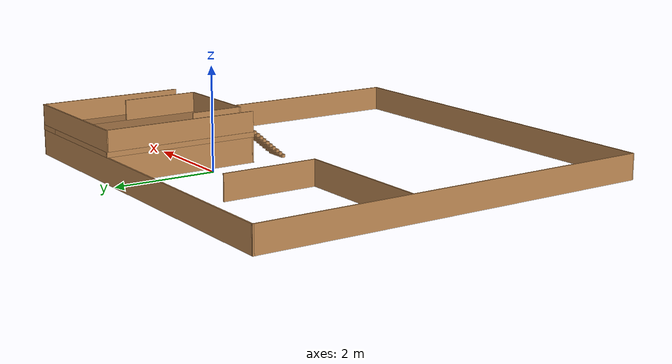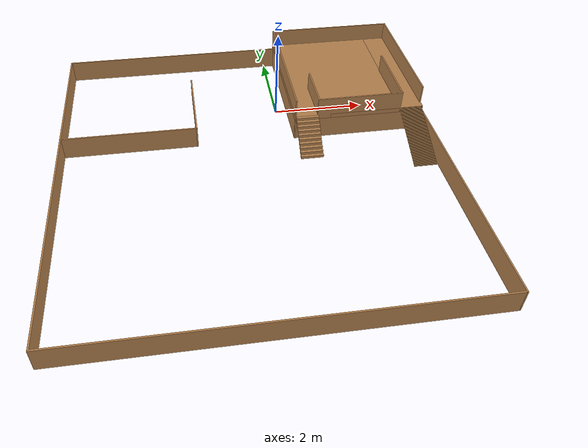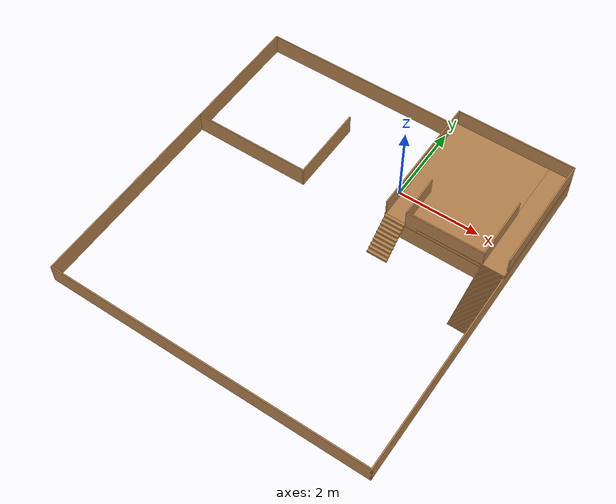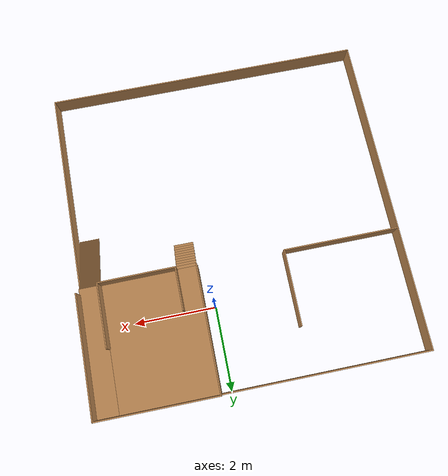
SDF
<?xml version='1.0'?>
<sdf version='1.7'>
  <model name='arena'>
    <pose>-0.8295 -1.99377 0 0 -0 0</pose>
    <link name='Floor_6'>
      <pose>2.49692 2.49323 0.5 0 -0 0</pose>
      <visual name='Floor_6_Visual_0'>
        <pose>-1.42421 0 0.05 0 -0 0</pose>
        <geometry>
          <box>
            <size>0.02684 3.05003 0.1</size>
          </box>
        </geometry>
        <material>
          <script>
            <uri>file://media/materials/scripts/gazebo.material</uri>
            <name>Gazebo/Wood</name>
          </script>
          <ambient>1 1 1 1</ambient>
        </material>
        <meta>
          <layer>1</layer>
        </meta>
      </visual>
      <collision name='Floor_6_Collision_0'>
        <geometry>
          <box>
            <size>0.02684 3.05003 0.1</size>
          </box>
        </geometry>
        <pose>-1.42421 0 0.05 0 -0 0</pose>
      </collision>
      <visual name='Floor_6_Visual_1'>
        <pose>-0.254024 0.000799 0.05 0 -0 0</pose>
        <geometry>
          <box>
            <size>2.31354 3.04843 0.1</size>
          </box>
        </geometry>
        <material>
          <script>
            <uri>file://media/materials/scripts/gazebo.material</uri>
            <name>Gazebo/Wood</name>
          </script>
          <ambient>1 1 1 1</ambient>
        </material>
        <meta>
          <layer>1</layer>
        </meta>
      </visual>
      <collision name='Floor_6_Collision_1'>
        <geometry>
          <box>
            <size>2.31354 3.04843 0.1</size>
          </box>
        </geometry>
        <pose>-0.254024 0.000799 0.05 0 -0 0</pose>
      </collision>
      <visual name='Floor_6_Visual_2'>
        <pose>1.17019 0.008605 0.05 0 -0 0</pose>
        <geometry>
          <box>
            <size>0.534887 3.03282 0.1</size>
          </box>
        </geometry>
        <material>
          <script>
            <uri>file://media/materials/scripts/gazebo.material</uri>
            <name>Gazebo/Wood</name>
          </script>
          <ambient>1 1 1 1</ambient>
        </material>
        <meta>
          <layer>1</layer>
        </meta>
      </visual>
      <collision name='Floor_6_Collision_2'>
        <geometry>
          <box>
            <size>0.534887 3.03282 0.1</size>
          </box>
        </geometry>
        <pose>1.17019 0.008605 0.05 0 -0 0</pose>
      </collision>
    </link>
    <link name='Stairs_11'>
      <visual name='Stairs_11_Visual_0'>
        <pose>3.65016 -0.298124 0.003 0 0 -3.14159</pose>
        <geometry>
          <box>
            <size>0.501 0.0129 0.006</size>
          </box>
        </geometry>
        <material>
          <script>
            <uri>file://media/materials/scripts/gazebo.material</uri>
            <name>Gazebo/Wood</name>
          </script>
          <ambient>1 1 1 1</ambient>
        </material>
        <meta>
          <layer>0</layer>
        </meta>
      </visual>
      <collision name='Stairs_11_Collision_0'>
        <geometry>
          <box>
            <size>0.501 0.0129 0.006</size>
          </box>
        </geometry>
        <pose>3.65016 -0.298124 0.003 0 0 -3.14159</pose>
      </collision>
      <visual name='Stairs_11_Visual_1'>
        <pose>3.65016 -0.285224 0.009 0 0 -3.14159</pose>
        <geometry>
          <box>
            <size>0.501 0.0129 0.006</size>
          </box>
        </geometry>
        <material>
          <script>
            <uri>file://media/materials/scripts/gazebo.material</uri>
            <name>Gazebo/Wood</name>
          </script>
          <ambient>1 1 1 1</ambient>
        </material>
        <meta>
          <layer>0</layer>
        </meta>
      </visual>
      <collision name='Stairs_11_Collision_1'>
        <geometry>
          <box>
            <size>0.501 0.0129 0.006</size>
          </box>
        </geometry>
        <pose>3.65016 -0.285224 0.009 0 0 -3.14159</pose>
      </collision>
      <visual name='Stairs_11_Visual_2'>
        <pose>3.65016 -0.272324 0.015 0 0 -3.14159</pose>
        <geometry>
          <box>
            <size>0.501 0.0129 0.006</size>
          </box>
        </geometry>
        <material>
          <script>
            <uri>file://media/materials/scripts/gazebo.material</uri>
            <name>Gazebo/Wood</name>
          </script>
          <ambient>1 1 1 1</ambient>
        </material>
        <meta>
          <layer>0</layer>
        </meta>
      </visual>
      <collision name='Stairs_11_Collision_2'>
        <geometry>
          <box>
            <size>0.501 0.0129 0.006</size>
          </box>
        </geometry>
        <pose>3.65016 -0.272324 0.015 0 0 -3.14159</pose>
      </collision>
      <visual name='Stairs_11_Visual_3'>
        <pose>3.65016 -0.259424 0.021 0 0 -3.14159</pose>
        <geometry>
          <box>
            <size>0.501 0.0129 0.006</size>
          </box>
        </geometry>
        <material>
          <script>
            <uri>file://media/materials/scripts/gazebo.material</uri>
            <name>Gazebo/Wood</name>
          </script>
          <ambient>1 1 1 1</ambient>
        </material>
        <meta>
          <layer>0</layer>
        </meta>
      </visual>
      <collision name='Stairs_11_Collision_3'>
        <geometry>
          <box>
            <size>0.501 0.0129 0.006</size>
          </box>
        </geometry>
        <pose>3.65016 -0.259424 0.021 0 0 -3.14159</pose>
      </collision>
      <visual name='Stairs_11_Visual_4'>
        <pose>3.65016 -0.246524 0.027 0 0 -3.14159</pose>
        <geometry>
          <box>
            <size>0.501 0.0129 0.006</size>
          </box>
        </geometry>
        <material>
          <script>
            <uri>file://media/materials/scripts/gazebo.material</uri>
            <name>Gazebo/Wood</name>
          </script>
          <ambient>1 1 1 1</ambient>
        </material>
        <meta>
          <layer>0</layer>
        </meta>
      </visual>
      <collision name='Stairs_11_Collision_4'>
        <geometry>
          <box>
            <size>0.501 0.0129 0.006</size>
          </box>
        </geometry>
        <pose>3.65016 -0.246524 0.027 0 0 -3.14159</pose>
      </collision>
      <visual name='Stairs_11_Visual_5'>
        <pose>3.65016 -0.233624 0.033 0 0 -3.14159</pose>
        <geometry>
          <box>
            <size>0.501 0.0129 0.006</size>
          </box>
        </geometry>
        <material>
          <script>
            <uri>file://media/materials/scripts/gazebo.material</uri>
            <name>Gazebo/Wood</name>
          </script>
          <ambient>1 1 1 1</ambient>
        </material>
        <meta>
          <layer>0</layer>
        </meta>
      </visual>
      <collision name='Stairs_11_Collision_5'>
        <geometry>
          <box>
            <size>0.501 0.0129 0.006</size>
          </box>
        </geometry>
        <pose>3.65016 -0.233624 0.033 0 0 -3.14159</pose>
      </collision>
      <visual name='Stairs_11_Visual_6'>
        <pose>3.65016 -0.220724 0.039 0 0 -3.14159</pose>
        <geometry>
          <box>
            <size>0.501 0.0129 0.006</size>
          </box>
        </geometry>
        <material>
          <script>
            <uri>file://media/materials/scripts/gazebo.material</uri>
            <name>Gazebo/Wood</name>
          </script>
          <ambient>1 1 1 1</ambient>
        </material>
        <meta>
          <layer>0</layer>
        </meta>
      </visual>
      <collision name='Stairs_11_Collision_6'>
        <geometry>
          <box>
            <size>0.501 0.0129 0.006</size>
          </box>
        </geometry>
        <pose>3.65016 -0.220724 0.039 0 0 -3.14159</pose>
      </collision>
      <visual name='Stairs_11_Visual_7'>
        <pose>3.65016 -0.207824 0.045 0 0 -3.14159</pose>
        <geometry>
          <box>
            <size>0.501 0.0129 0.006</size>
          </box>
        </geometry>
        <material>
          <script>
            <uri>file://media/materials/scripts/gazebo.material</uri>
            <name>Gazebo/Wood</name>
          </script>
          <ambient>1 1 1 1</ambient>
        </material>
        <meta>
          <layer>0</layer>
        </meta>
      </visual>
      <collision name='Stairs_11_Collision_7'>
        <geometry>
          <box>
            <size>0.501 0.0129 0.006</size>
          </box>
        </geometry>
        <pose>3.65016 -0.207824 0.045 0 0 -3.14159</pose>
      </collision>
      <visual name='Stairs_11_Visual_8'>
        <pose>3.65016 -0.194924 0.051 0 0 -3.14159</pose>
        <geometry>
          <box>
            <size>0.501 0.0129 0.006</size>
          </box>
        </geometry>
        <material>
          <script>
            <uri>file://media/materials/scripts/gazebo.material</uri>
            <name>Gazebo/Wood</name>
          </script>
          <ambient>1 1 1 1</ambient>
        </material>
        <meta>
          <layer>0</layer>
        </meta>
      </visual>
      <collision name='Stairs_11_Collision_8'>
        <geometry>
          <box>
            <size>0.501 0.0129 0.006</size>
          </box>
        </geometry>
        <pose>3.65016 -0.194924 0.051 0 0 -3.14159</pose>
      </collision>
      <visual name='Stairs_11_Visual_9'>
        <pose>3.65016 -0.182024 0.057 0 0 -3.14159</pose>
        <geometry>
          <box>
            <size>0.501 0.0129 0.006</size>
          </box>
        </geometry>
        <material>
          <script>
            <uri>file://media/materials/scripts/gazebo.material</uri>
            <name>Gazebo/Wood</name>
          </script>
          <ambient>1 1 1 1</ambient>
        </material>
        <meta>
          <layer>0</layer>
        </meta>
      </visual>
      <collision name='Stairs_11_Collision_9'>
        <geometry>
          <box>
            <size>0.501 0.0129 0.006</size>
          </box>
        </geometry>
        <pose>3.65016 -0.182024 0.057 0 0 -3.14159</pose>
      </collision>
      <visual name='Stairs_11_Visual_10'>
        <pose>3.65016 -0.169124 0.063 0 0 -3.14159</pose>
        <geometry>
          <box>
            <size>0.501 0.0129 0.006</size>
          </box>
        </geometry>
        <material>
          <script>
            <uri>file://media/materials/scripts/gazebo.material</uri>
            <name>Gazebo/Wood</name>
          </script>
          <ambient>1 1 1 1</ambient>
        </material>
        <meta>
          <layer>0</layer>
        </meta>
      </visual>
      <collision name='Stairs_11_Collision_10'>
        <geometry>
          <box>
            <size>0.501 0.0129 0.006</size>
          </box>
        </geometry>
        <pose>3.65016 -0.169124 0.063 0 0 -3.14159</pose>
      </collision>
      <visual name='Stairs_11_Visual_11'>
        <pose>3.65016 -0.156224 0.069 0 0 -3.14159</pose>
        <geometry>
          <box>
            <size>0.501 0.0129 0.006</size>
          </box>
        </geometry>
        <material>
          <script>
            <uri>file://media/materials/scripts/gazebo.material</uri>
            <name>Gazebo/Wood</name>
          </script>
          <ambient>1 1 1 1</ambient>
        </material>
        <meta>
          <layer>0</layer>
        </meta>
      </visual>
      <collision name='Stairs_11_Collision_11'>
        <geometry>
          <box>
            <size>0.501 0.0129 0.006</size>
          </box>
        </geometry>
        <pose>3.65016 -0.156224 0.069 0 0 -3.14159</pose>
      </collision>
      <visual name='Stairs_11_Visual_12'>
        <pose>3.65016 -0.143324 0.075 0 0 -3.14159</pose>
        <geometry>
          <box>
            <size>0.501 0.0129 0.006</size>
          </box>
        </geometry>
        <material>
          <script>
            <uri>file://media/materials/scripts/gazebo.material</uri>
            <name>Gazebo/Wood</name>
          </script>
          <ambient>1 1 1 1</ambient>
        </material>
        <meta>
          <layer>0</layer>
        </meta>
      </visual>
      <collision name='Stairs_11_Collision_12'>
        <geometry>
          <box>
            <size>0.501 0.0129 0.006</size>
          </box>
        </geometry>
        <pose>3.65016 -0.143324 0.075 0 0 -3.14159</pose>
      </collision>
      <visual name='Stairs_11_Visual_13'>
        <pose>3.65016 -0.130424 0.081 0 0 -3.14159</pose>
        <geometry>
          <box>
            <size>0.501 0.0129 0.006</size>
          </box>
        </geometry>
        <material>
          <script>
            <uri>file://media/materials/scripts/gazebo.material</uri>
            <name>Gazebo/Wood</name>
          </script>
          <ambient>1 1 1 1</ambient>
        </material>
        <meta>
          <layer>0</layer>
        </meta>
      </visual>
      <collision name='Stairs_11_Collision_13'>
        <geometry>
          <box>
            <size>0.501 0.0129 0.006</size>
          </box>
        </geometry>
        <pose>3.65016 -0.130424 0.081 0 0 -3.14159</pose>
      </collision>
      <visual name='Stairs_11_Visual_14'>
        <pose>3.65016 -0.117524 0.087 0 0 -3.14159</pose>
        <geometry>
          <box>
            <size>0.501 0.0129 0.006</size>
          </box>
        </geometry>
        <material>
          <script>
            <uri>file://media/materials/scripts/gazebo.material</uri>
            <name>Gazebo/Wood</name>
          </script>
          <ambient>1 1 1 1</ambient>
        </material>
        <meta>
          <layer>0</layer>
        </meta>
      </visual>
      <collision name='Stairs_11_Collision_14'>
        <geometry>
          <box>
            <size>0.501 0.0129 0.006</size>
          </box>
        </geometry>
        <pose>3.65016 -0.117524 0.087 0 0 -3.14159</pose>
      </collision>
      <visual name='Stairs_11_Visual_15'>
        <pose>3.65016 -0.104624 0.093 0 0 -3.14159</pose>
        <geometry>
          <box>
            <size>0.501 0.0129 0.006</size>
          </box>
        </geometry>
        <material>
          <script>
            <uri>file://media/materials/scripts/gazebo.material</uri>
            <name>Gazebo/Wood</name>
          </script>
          <ambient>1 1 1 1</ambient>
        </material>
        <meta>
          <layer>0</layer>
        </meta>
      </visual>
      <collision name='Stairs_11_Collision_15'>
        <geometry>
          <box>
            <size>0.501 0.0129 0.006</size>
          </box>
        </geometry>
        <pose>3.65016 -0.104624 0.093 0 0 -3.14159</pose>
      </collision>
      <visual name='Stairs_11_Visual_16'>
        <pose>3.65016 -0.091724 0.099 0 0 -3.14159</pose>
        <geometry>
          <box>
            <size>0.501 0.0129 0.006</size>
          </box>
        </geometry>
        <material>
          <script>
            <uri>file://media/materials/scripts/gazebo.material</uri>
            <name>Gazebo/Wood</name>
          </script>
          <ambient>1 1 1 1</ambient>
        </material>
        <meta>
          <layer>0</layer>
        </meta>
      </visual>
      <collision name='Stairs_11_Collision_16'>
        <geometry>
          <box>
            <size>0.501 0.0129 0.006</size>
          </box>
        </geometry>
        <pose>3.65016 -0.091724 0.099 0 0 -3.14159</pose>
      </collision>
      <visual name='Stairs_11_Visual_17'>
        <pose>3.65016 -0.078824 0.105 0 0 -3.14159</pose>
        <geometry>
          <box>
            <size>0.501 0.0129 0.006</size>
          </box>
        </geometry>
        <material>
          <script>
            <uri>file://media/materials/scripts/gazebo.material</uri>
            <name>Gazebo/Wood</name>
          </script>
          <ambient>1 1 1 1</ambient>
        </material>
        <meta>
          <layer>0</layer>
        </meta>
      </visual>
      <collision name='Stairs_11_Collision_17'>
        <geometry>
          <box>
            <size>0.501 0.0129 0.006</size>
          </box>
        </geometry>
        <pose>3.65016 -0.078824 0.105 0 0 -3.14159</pose>
      </collision>
      <visual name='Stairs_11_Visual_18'>
        <pose>3.65016 -0.065924 0.111 0 0 -3.14159</pose>
        <geometry>
          <box>
            <size>0.501 0.0129 0.006</size>
          </box>
        </geometry>
        <material>
          <script>
            <uri>file://media/materials/scripts/gazebo.material</uri>
            <name>Gazebo/Wood</name>
          </script>
          <ambient>1 1 1 1</ambient>
        </material>
        <meta>
          <layer>0</layer>
        </meta>
      </visual>
      <collision name='Stairs_11_Collision_18'>
        <geometry>
          <box>
            <size>0.501 0.0129 0.006</size>
          </box>
        </geometry>
        <pose>3.65016 -0.065924 0.111 0 0 -3.14159</pose>
      </collision>
      <visual name='Stairs_11_Visual_19'>
        <pose>3.65016 -0.053024 0.117 0 0 -3.14159</pose>
        <geometry>
          <box>
            <size>0.501 0.0129 0.006</size>
          </box>
        </geometry>
        <material>
          <script>
            <uri>file://media/materials/scripts/gazebo.material</uri>
            <name>Gazebo/Wood</name>
          </script>
          <ambient>1 1 1 1</ambient>
        </material>
        <meta>
          <layer>0</layer>
        </meta>
      </visual>
      <collision name='Stairs_11_Collision_19'>
        <geometry>
          <box>
            <size>0.501 0.0129 0.006</size>
          </box>
        </geometry>
        <pose>3.65016 -0.053024 0.117 0 0 -3.14159</pose>
      </collision>
      <visual name='Stairs_11_Visual_20'>
        <pose>3.65016 -0.040124 0.123 0 0 -3.14159</pose>
        <geometry>
          <box>
            <size>0.501 0.0129 0.006</size>
          </box>
        </geometry>
        <material>
          <script>
            <uri>file://media/materials/scripts/gazebo.material</uri>
            <name>Gazebo/Wood</name>
          </script>
          <ambient>1 1 1 1</ambient>
        </material>
        <meta>
          <layer>0</layer>
        </meta>
      </visual>
      <collision name='Stairs_11_Collision_20'>
        <geometry>
          <box>
            <size>0.501 0.0129 0.006</size>
          </box>
        </geometry>
        <pose>3.65016 -0.040124 0.123 0 0 -3.14159</pose>
      </collision>
      <visual name='Stairs_11_Visual_21'>
        <pose>3.65016 -0.027224 0.129 0 0 -3.14159</pose>
        <geometry>
          <box>
            <size>0.501 0.0129 0.006</size>
          </box>
        </geometry>
        <material>
          <script>
            <uri>file://media/materials/scripts/gazebo.material</uri>
            <name>Gazebo/Wood</name>
          </script>
          <ambient>1 1 1 1</ambient>
        </material>
        <meta>
          <layer>0</layer>
        </meta>
      </visual>
      <collision name='Stairs_11_Collision_21'>
        <geometry>
          <box>
            <size>0.501 0.0129 0.006</size>
          </box>
        </geometry>
        <pose>3.65016 -0.027224 0.129 0 0 -3.14159</pose>
      </collision>
      <visual name='Stairs_11_Visual_22'>
        <pose>3.65016 -0.014324 0.135 0 0 -3.14159</pose>
        <geometry>
          <box>
            <size>0.501 0.0129 0.006</size>
          </box>
        </geometry>
        <material>
          <script>
            <uri>file://media/materials/scripts/gazebo.material</uri>
            <name>Gazebo/Wood</name>
          </script>
          <ambient>1 1 1 1</ambient>
        </material>
        <meta>
          <layer>0</layer>
        </meta>
      </visual>
      <collision name='Stairs_11_Collision_22'>
        <geometry>
          <box>
            <size>0.501 0.0129 0.006</size>
          </box>
        </geometry>
        <pose>3.65016 -0.014324 0.135 0 0 -3.14159</pose>
      </collision>
      <visual name='Stairs_11_Visual_23'>
        <pose>3.65016 -0.001424 0.141 0 0 -3.14159</pose>
        <geometry>
          <box>
            <size>0.501 0.0129 0.006</size>
          </box>
        </geometry>
        <material>
          <script>
            <uri>file://media/materials/scripts/gazebo.material</uri>
            <name>Gazebo/Wood</name>
          </script>
          <ambient>1 1 1 1</ambient>
        </material>
        <meta>
          <layer>0</layer>
        </meta>
      </visual>
      <collision name='Stairs_11_Collision_23'>
        <geometry>
          <box>
            <size>0.501 0.0129 0.006</size>
          </box>
        </geometry>
        <pose>3.65016 -0.001424 0.141 0 0 -3.14159</pose>
      </collision>
      <visual name='Stairs_11_Visual_24'>
        <pose>3.65016 0.011476 0.147 0 0 -3.14159</pose>
        <geometry>
          <box>
            <size>0.501 0.0129 0.006</size>
          </box>
        </geometry>
        <material>
          <script>
            <uri>file://media/materials/scripts/gazebo.material</uri>
            <name>Gazebo/Wood</name>
          </script>
          <ambient>1 1 1 1</ambient>
        </material>
        <meta>
          <layer>0</layer>
        </meta>
      </visual>
      <collision name='Stairs_11_Collision_24'>
        <geometry>
          <box>
            <size>0.501 0.0129 0.006</size>
          </box>
        </geometry>
        <pose>3.65016 0.011476 0.147 0 0 -3.14159</pose>
      </collision>
      <visual name='Stairs_11_Visual_25'>
        <pose>3.65016 0.024376 0.153 0 0 -3.14159</pose>
        <geometry>
          <box>
            <size>0.501 0.0129 0.006</size>
          </box>
        </geometry>
        <material>
          <script>
            <uri>file://media/materials/scripts/gazebo.material</uri>
            <name>Gazebo/Wood</name>
          </script>
          <ambient>1 1 1 1</ambient>
        </material>
        <meta>
          <layer>0</layer>
        </meta>
      </visual>
      <collision name='Stairs_11_Collision_25'>
        <geometry>
          <box>
            <size>0.501 0.0129 0.006</size>
          </box>
        </geometry>
        <pose>3.65016 0.024376 0.153 0 0 -3.14159</pose>
      </collision>
      <visual name='Stairs_11_Visual_26'>
        <pose>3.65016 0.037276 0.159 0 0 -3.14159</pose>
        <geometry>
          <box>
            <size>0.501 0.0129 0.006</size>
          </box>
        </geometry>
        <material>
          <script>
            <uri>file://media/materials/scripts/gazebo.material</uri>
            <name>Gazebo/Wood</name>
          </script>
          <ambient>1 1 1 1</ambient>
        </material>
        <meta>
          <layer>0</layer>
        </meta>
      </visual>
      <collision name='Stairs_11_Collision_26'>
        <geometry>
          <box>
            <size>0.501 0.0129 0.006</size>
          </box>
        </geometry>
        <pose>3.65016 0.037276 0.159 0 0 -3.14159</pose>
      </collision>
      <visual name='Stairs_11_Visual_27'>
        <pose>3.65016 0.050176 0.165 0 0 -3.14159</pose>
        <geometry>
          <box>
            <size>0.501 0.0129 0.006</size>
          </box>
        </geometry>
        <material>
          <script>
            <uri>file://media/materials/scripts/gazebo.material</uri>
            <name>Gazebo/Wood</name>
          </script>
          <ambient>1 1 1 1</ambient>
        </material>
        <meta>
          <layer>0</layer>
        </meta>
      </visual>
      <collision name='Stairs_11_Collision_27'>
        <geometry>
          <box>
            <size>0.501 0.0129 0.006</size>
          </box>
        </geometry>
        <pose>3.65016 0.050176 0.165 0 0 -3.14159</pose>
      </collision>
      <visual name='Stairs_11_Visual_28'>
        <pose>3.65016 0.063076 0.171 0 0 -3.14159</pose>
        <geometry>
          <box>
            <size>0.501 0.0129 0.006</size>
          </box>
        </geometry>
        <material>
          <script>
            <uri>file://media/materials/scripts/gazebo.material</uri>
            <name>Gazebo/Wood</name>
          </script>
          <ambient>1 1 1 1</ambient>
        </material>
        <meta>
          <layer>0</layer>
        </meta>
      </visual>
      <collision name='Stairs_11_Collision_28'>
        <geometry>
          <box>
            <size>0.501 0.0129 0.006</size>
          </box>
        </geometry>
        <pose>3.65016 0.063076 0.171 0 0 -3.14159</pose>
      </collision>
      <visual name='Stairs_11_Visual_29'>
        <pose>3.65016 0.075976 0.177 0 0 -3.14159</pose>
        <geometry>
          <box>
            <size>0.501 0.0129 0.006</size>
          </box>
        </geometry>
        <material>
          <script>
            <uri>file://media/materials/scripts/gazebo.material</uri>
            <name>Gazebo/Wood</name>
          </script>
          <ambient>1 1 1 1</ambient>
        </material>
        <meta>
          <layer>0</layer>
        </meta>
      </visual>
      <collision name='Stairs_11_Collision_29'>
        <geometry>
          <box>
            <size>0.501 0.0129 0.006</size>
          </box>
        </geometry>
        <pose>3.65016 0.075976 0.177 0 0 -3.14159</pose>
      </collision>
      <visual name='Stairs_11_Visual_30'>
        <pose>3.65016 0.088876 0.183 0 0 -3.14159</pose>
        <geometry>
          <box>
            <size>0.501 0.0129 0.006</size>
          </box>
        </geometry>
        <material>
          <script>
            <uri>file://media/materials/scripts/gazebo.material</uri>
            <name>Gazebo/Wood</name>
          </script>
          <ambient>1 1 1 1</ambient>
        </material>
        <meta>
          <layer>0</layer>
        </meta>
      </visual>
      <collision name='Stairs_11_Collision_30'>
        <geometry>
          <box>
            <size>0.501 0.0129 0.006</size>
          </box>
        </geometry>
        <pose>3.65016 0.088876 0.183 0 0 -3.14159</pose>
      </collision>
      <visual name='Stairs_11_Visual_31'>
        <pose>3.65016 0.101776 0.189 0 0 -3.14159</pose>
        <geometry>
          <box>
            <size>0.501 0.0129 0.006</size>
          </box>
        </geometry>
        <material>
          <script>
            <uri>file://media/materials/scripts/gazebo.material</uri>
            <name>Gazebo/Wood</name>
          </script>
          <ambient>1 1 1 1</ambient>
        </material>
        <meta>
          <layer>0</layer>
        </meta>
      </visual>
      <collision name='Stairs_11_Collision_31'>
        <geometry>
          <box>
            <size>0.501 0.0129 0.006</size>
          </box>
        </geometry>
        <pose>3.65016 0.101776 0.189 0 0 -3.14159</pose>
      </collision>
      <visual name='Stairs_11_Visual_32'>
        <pose>3.65016 0.114676 0.195 0 0 -3.14159</pose>
        <geometry>
          <box>
            <size>0.501 0.0129 0.006</size>
          </box>
        </geometry>
        <material>
          <script>
            <uri>file://media/materials/scripts/gazebo.material</uri>
            <name>Gazebo/Wood</name>
          </script>
          <ambient>1 1 1 1</ambient>
        </material>
        <meta>
          <layer>0</layer>
        </meta>
      </visual>
      <collision name='Stairs_11_Collision_32'>
        <geometry>
          <box>
            <size>0.501 0.0129 0.006</size>
          </box>
        </geometry>
        <pose>3.65016 0.114676 0.195 0 0 -3.14159</pose>
      </collision>
      <visual name='Stairs_11_Visual_33'>
        <pose>3.65016 0.127576 0.201 0 0 -3.14159</pose>
        <geometry>
          <box>
            <size>0.501 0.0129 0.006</size>
          </box>
        </geometry>
        <material>
          <script>
            <uri>file://media/materials/scripts/gazebo.material</uri>
            <name>Gazebo/Wood</name>
          </script>
          <ambient>1 1 1 1</ambient>
        </material>
        <meta>
          <layer>0</layer>
        </meta>
      </visual>
      <collision name='Stairs_11_Collision_33'>
        <geometry>
          <box>
            <size>0.501 0.0129 0.006</size>
          </box>
        </geometry>
        <pose>3.65016 0.127576 0.201 0 0 -3.14159</pose>
      </collision>
      <visual name='Stairs_11_Visual_34'>
        <pose>3.65016 0.140476 0.207 0 0 -3.14159</pose>
        <geometry>
          <box>
            <size>0.501 0.0129 0.006</size>
          </box>
        </geometry>
        <material>
          <script>
            <uri>file://media/materials/scripts/gazebo.material</uri>
            <name>Gazebo/Wood</name>
          </script>
          <ambient>1 1 1 1</ambient>
        </material>
        <meta>
          <layer>0</layer>
        </meta>
      </visual>
      <collision name='Stairs_11_Collision_34'>
        <geometry>
          <box>
            <size>0.501 0.0129 0.006</size>
          </box>
        </geometry>
        <pose>3.65016 0.140476 0.207 0 0 -3.14159</pose>
      </collision>
      <visual name='Stairs_11_Visual_35'>
        <pose>3.65016 0.153376 0.213 0 0 -3.14159</pose>
        <geometry>
          <box>
            <size>0.501 0.0129 0.006</size>
          </box>
        </geometry>
        <material>
          <script>
            <uri>file://media/materials/scripts/gazebo.material</uri>
            <name>Gazebo/Wood</name>
          </script>
          <ambient>1 1 1 1</ambient>
        </material>
        <meta>
          <layer>0</layer>
        </meta>
      </visual>
      <collision name='Stairs_11_Collision_35'>
        <geometry>
          <box>
            <size>0.501 0.0129 0.006</size>
          </box>
        </geometry>
        <pose>3.65016 0.153376 0.213 0 0 -3.14159</pose>
      </collision>
      <visual name='Stairs_11_Visual_36'>
        <pose>3.65016 0.166276 0.219 0 0 -3.14159</pose>
        <geometry>
          <box>
            <size>0.501 0.0129 0.006</size>
          </box>
        </geometry>
        <material>
          <script>
            <uri>file://media/materials/scripts/gazebo.material</uri>
            <name>Gazebo/Wood</name>
          </script>
          <ambient>1 1 1 1</ambient>
        </material>
        <meta>
          <layer>0</layer>
        </meta>
      </visual>
      <collision name='Stairs_11_Collision_36'>
        <geometry>
          <box>
            <size>0.501 0.0129 0.006</size>
          </box>
        </geometry>
        <pose>3.65016 0.166276 0.219 0 0 -3.14159</pose>
      </collision>
      <visual name='Stairs_11_Visual_37'>
        <pose>3.65016 0.179176 0.225 0 0 -3.14159</pose>
        <geometry>
          <box>
            <size>0.501 0.0129 0.006</size>
          </box>
        </geometry>
        <material>
          <script>
            <uri>file://media/materials/scripts/gazebo.material</uri>
            <name>Gazebo/Wood</name>
          </script>
          <ambient>1 1 1 1</ambient>
        </material>
        <meta>
          <layer>0</layer>
        </meta>
      </visual>
      <collision name='Stairs_11_Collision_37'>
        <geometry>
          <box>
            <size>0.501 0.0129 0.006</size>
          </box>
        </geometry>
        <pose>3.65016 0.179176 0.225 0 0 -3.14159</pose>
      </collision>
      <visual name='Stairs_11_Visual_38'>
        <pose>3.65016 0.192076 0.231 0 0 -3.14159</pose>
        <geometry>
          <box>
            <size>0.501 0.0129 0.006</size>
          </box>
        </geometry>
        <material>
          <script>
            <uri>file://media/materials/scripts/gazebo.material</uri>
            <name>Gazebo/Wood</name>
          </script>
          <ambient>1 1 1 1</ambient>
        </material>
        <meta>
          <layer>0</layer>
        </meta>
      </visual>
      <collision name='Stairs_11_Collision_38'>
        <geometry>
          <box>
            <size>0.501 0.0129 0.006</size>
          </box>
        </geometry>
        <pose>3.65016 0.192076 0.231 0 0 -3.14159</pose>
      </collision>
      <visual name='Stairs_11_Visual_39'>
        <pose>3.65016 0.204976 0.237 0 0 -3.14159</pose>
        <geometry>
          <box>
            <size>0.501 0.0129 0.006</size>
          </box>
        </geometry>
        <material>
          <script>
            <uri>file://media/materials/scripts/gazebo.material</uri>
            <name>Gazebo/Wood</name>
          </script>
          <ambient>1 1 1 1</ambient>
        </material>
        <meta>
          <layer>0</layer>
        </meta>
      </visual>
      <collision name='Stairs_11_Collision_39'>
        <geometry>
          <box>
            <size>0.501 0.0129 0.006</size>
          </box>
        </geometry>
        <pose>3.65016 0.204976 0.237 0 0 -3.14159</pose>
      </collision>
      <visual name='Stairs_11_Visual_40'>
        <pose>3.65016 0.217876 0.243 0 0 -3.14159</pose>
        <geometry>
          <box>
            <size>0.501 0.0129 0.006</size>
          </box>
        </geometry>
        <material>
          <script>
            <uri>file://media/materials/scripts/gazebo.material</uri>
            <name>Gazebo/Wood</name>
          </script>
          <ambient>1 1 1 1</ambient>
        </material>
        <meta>
          <layer>0</layer>
        </meta>
      </visual>
      <collision name='Stairs_11_Collision_40'>
        <geometry>
          <box>
            <size>0.501 0.0129 0.006</size>
          </box>
        </geometry>
        <pose>3.65016 0.217876 0.243 0 0 -3.14159</pose>
      </collision>
      <visual name='Stairs_11_Visual_41'>
        <pose>3.65016 0.230776 0.249 0 0 -3.14159</pose>
        <geometry>
          <box>
            <size>0.501 0.0129 0.006</size>
          </box>
        </geometry>
        <material>
          <script>
            <uri>file://media/materials/scripts/gazebo.material</uri>
            <name>Gazebo/Wood</name>
          </script>
          <ambient>1 1 1 1</ambient>
        </material>
        <meta>
          <layer>0</layer>
        </meta>
      </visual>
      <collision name='Stairs_11_Collision_41'>
        <geometry>
          <box>
            <size>0.501 0.0129 0.006</size>
          </box>
        </geometry>
        <pose>3.65016 0.230776 0.249 0 0 -3.14159</pose>
      </collision>
      <visual name='Stairs_11_Visual_42'>
        <pose>3.65016 0.243676 0.255 0 0 -3.14159</pose>
        <geometry>
          <box>
            <size>0.501 0.0129 0.006</size>
          </box>
        </geometry>
        <material>
          <script>
            <uri>file://media/materials/scripts/gazebo.material</uri>
            <name>Gazebo/Wood</name>
          </script>
          <ambient>1 1 1 1</ambient>
        </material>
        <meta>
          <layer>0</layer>
        </meta>
      </visual>
      <collision name='Stairs_11_Collision_42'>
        <geometry>
          <box>
            <size>0.501 0.0129 0.006</size>
          </box>
        </geometry>
        <pose>3.65016 0.243676 0.255 0 0 -3.14159</pose>
      </collision>
      <visual name='Stairs_11_Visual_43'>
        <pose>3.65016 0.256576 0.261 0 0 -3.14159</pose>
        <geometry>
          <box>
            <size>0.501 0.0129 0.006</size>
          </box>
        </geometry>
        <material>
          <script>
            <uri>file://media/materials/scripts/gazebo.material</uri>
            <name>Gazebo/Wood</name>
          </script>
          <ambient>1 1 1 1</ambient>
        </material>
        <meta>
          <layer>0</layer>
        </meta>
      </visual>
      <collision name='Stairs_11_Collision_43'>
        <geometry>
          <box>
            <size>0.501 0.0129 0.006</size>
          </box>
        </geometry>
        <pose>3.65016 0.256576 0.261 0 0 -3.14159</pose>
      </collision>
      <visual name='Stairs_11_Visual_44'>
        <pose>3.65016 0.269476 0.267 0 0 -3.14159</pose>
        <geometry>
          <box>
            <size>0.501 0.0129 0.006</size>
          </box>
        </geometry>
        <material>
          <script>
            <uri>file://media/materials/scripts/gazebo.material</uri>
            <name>Gazebo/Wood</name>
          </script>
          <ambient>1 1 1 1</ambient>
        </material>
        <meta>
          <layer>0</layer>
        </meta>
      </visual>
      <collision name='Stairs_11_Collision_44'>
        <geometry>
          <box>
            <size>0.501 0.0129 0.006</size>
          </box>
        </geometry>
        <pose>3.65016 0.269476 0.267 0 0 -3.14159</pose>
      </collision>
      <visual name='Stairs_11_Visual_45'>
        <pose>3.65016 0.282376 0.273 0 0 -3.14159</pose>
        <geometry>
          <box>
            <size>0.501 0.0129 0.006</size>
          </box>
        </geometry>
        <material>
          <script>
            <uri>file://media/materials/scripts/gazebo.material</uri>
            <name>Gazebo/Wood</name>
          </script>
          <ambient>1 1 1 1</ambient>
        </material>
        <meta>
          <layer>0</layer>
        </meta>
      </visual>
      <collision name='Stairs_11_Collision_45'>
        <geometry>
          <box>
            <size>0.501 0.0129 0.006</size>
          </box>
        </geometry>
        <pose>3.65016 0.282376 0.273 0 0 -3.14159</pose>
      </collision>
      <visual name='Stairs_11_Visual_46'>
        <pose>3.65016 0.295276 0.279 0 0 -3.14159</pose>
        <geometry>
          <box>
            <size>0.501 0.0129 0.006</size>
          </box>
        </geometry>
        <material>
          <script>
            <uri>file://media/materials/scripts/gazebo.material</uri>
            <name>Gazebo/Wood</name>
          </script>
          <ambient>1 1 1 1</ambient>
        </material>
        <meta>
          <layer>0</layer>
        </meta>
      </visual>
      <collision name='Stairs_11_Collision_46'>
        <geometry>
          <box>
            <size>0.501 0.0129 0.006</size>
          </box>
        </geometry>
        <pose>3.65016 0.295276 0.279 0 0 -3.14159</pose>
      </collision>
      <visual name='Stairs_11_Visual_47'>
        <pose>3.65016 0.308176 0.285 0 0 -3.14159</pose>
        <geometry>
          <box>
            <size>0.501 0.0129 0.006</size>
          </box>
        </geometry>
        <material>
          <script>
            <uri>file://media/materials/scripts/gazebo.material</uri>
            <name>Gazebo/Wood</name>
          </script>
          <ambient>1 1 1 1</ambient>
        </material>
        <meta>
          <layer>0</layer>
        </meta>
      </visual>
      <collision name='Stairs_11_Collision_47'>
        <geometry>
          <box>
            <size>0.501 0.0129 0.006</size>
          </box>
        </geometry>
        <pose>3.65016 0.308176 0.285 0 0 -3.14159</pose>
      </collision>
      <visual name='Stairs_11_Visual_48'>
        <pose>3.65016 0.321076 0.291 0 0 -3.14159</pose>
        <geometry>
          <box>
            <size>0.501 0.0129 0.006</size>
          </box>
        </geometry>
        <material>
          <script>
            <uri>file://media/materials/scripts/gazebo.material</uri>
            <name>Gazebo/Wood</name>
          </script>
          <ambient>1 1 1 1</ambient>
        </material>
        <meta>
          <layer>0</layer>
        </meta>
      </visual>
      <collision name='Stairs_11_Collision_48'>
        <geometry>
          <box>
            <size>0.501 0.0129 0.006</size>
          </box>
        </geometry>
        <pose>3.65016 0.321076 0.291 0 0 -3.14159</pose>
      </collision>
      <visual name='Stairs_11_Visual_49'>
        <pose>3.65016 0.333976 0.297 0 0 -3.14159</pose>
        <geometry>
          <box>
            <size>0.501 0.0129 0.006</size>
          </box>
        </geometry>
        <material>
          <script>
            <uri>file://media/materials/scripts/gazebo.material</uri>
            <name>Gazebo/Wood</name>
          </script>
          <ambient>1 1 1 1</ambient>
        </material>
        <meta>
          <layer>0</layer>
        </meta>
      </visual>
      <collision name='Stairs_11_Collision_49'>
        <geometry>
          <box>
            <size>0.501 0.0129 0.006</size>
          </box>
        </geometry>
        <pose>3.65016 0.333976 0.297 0 0 -3.14159</pose>
      </collision>
      <visual name='Stairs_11_Visual_50'>
        <pose>3.65016 0.346876 0.303 0 0 -3.14159</pose>
        <geometry>
          <box>
            <size>0.501 0.0129 0.006</size>
          </box>
        </geometry>
        <material>
          <script>
            <uri>file://media/materials/scripts/gazebo.material</uri>
            <name>Gazebo/Wood</name>
          </script>
          <ambient>1 1 1 1</ambient>
        </material>
        <meta>
          <layer>0</layer>
        </meta>
      </visual>
      <collision name='Stairs_11_Collision_50'>
        <geometry>
          <box>
            <size>0.501 0.0129 0.006</size>
          </box>
        </geometry>
        <pose>3.65016 0.346876 0.303 0 0 -3.14159</pose>
      </collision>
      <visual name='Stairs_11_Visual_51'>
        <pose>3.65016 0.359776 0.309 0 0 -3.14159</pose>
        <geometry>
          <box>
            <size>0.501 0.0129 0.006</size>
          </box>
        </geometry>
        <material>
          <script>
            <uri>file://media/materials/scripts/gazebo.material</uri>
            <name>Gazebo/Wood</name>
          </script>
          <ambient>1 1 1 1</ambient>
        </material>
        <meta>
          <layer>0</layer>
        </meta>
      </visual>
      <collision name='Stairs_11_Collision_51'>
        <geometry>
          <box>
            <size>0.501 0.0129 0.006</size>
          </box>
        </geometry>
        <pose>3.65016 0.359776 0.309 0 0 -3.14159</pose>
      </collision>
      <visual name='Stairs_11_Visual_52'>
        <pose>3.65016 0.372676 0.315 0 0 -3.14159</pose>
        <geometry>
          <box>
            <size>0.501 0.0129 0.006</size>
          </box>
        </geometry>
        <material>
          <script>
            <uri>file://media/materials/scripts/gazebo.material</uri>
            <name>Gazebo/Wood</name>
          </script>
          <ambient>1 1 1 1</ambient>
        </material>
        <meta>
          <layer>0</layer>
        </meta>
      </visual>
      <collision name='Stairs_11_Collision_52'>
        <geometry>
          <box>
            <size>0.501 0.0129 0.006</size>
          </box>
        </geometry>
        <pose>3.65016 0.372676 0.315 0 0 -3.14159</pose>
      </collision>
      <visual name='Stairs_11_Visual_53'>
        <pose>3.65016 0.385576 0.321 0 0 -3.14159</pose>
        <geometry>
          <box>
            <size>0.501 0.0129 0.006</size>
          </box>
        </geometry>
        <material>
          <script>
            <uri>file://media/materials/scripts/gazebo.material</uri>
            <name>Gazebo/Wood</name>
          </script>
          <ambient>1 1 1 1</ambient>
        </material>
        <meta>
          <layer>0</layer>
        </meta>
      </visual>
      <collision name='Stairs_11_Collision_53'>
        <geometry>
          <box>
            <size>0.501 0.0129 0.006</size>
          </box>
        </geometry>
        <pose>3.65016 0.385576 0.321 0 0 -3.14159</pose>
      </collision>
      <visual name='Stairs_11_Visual_54'>
        <pose>3.65016 0.398476 0.327 0 0 -3.14159</pose>
        <geometry>
          <box>
            <size>0.501 0.0129 0.006</size>
          </box>
        </geometry>
        <material>
          <script>
            <uri>file://media/materials/scripts/gazebo.material</uri>
            <name>Gazebo/Wood</name>
          </script>
          <ambient>1 1 1 1</ambient>
        </material>
        <meta>
          <layer>0</layer>
        </meta>
      </visual>
      <collision name='Stairs_11_Collision_54'>
        <geometry>
          <box>
            <size>0.501 0.0129 0.006</size>
          </box>
        </geometry>
        <pose>3.65016 0.398476 0.327 0 0 -3.14159</pose>
      </collision>
      <visual name='Stairs_11_Visual_55'>
        <pose>3.65016 0.411376 0.333 0 0 -3.14159</pose>
        <geometry>
          <box>
            <size>0.501 0.0129 0.006</size>
          </box>
        </geometry>
        <material>
          <script>
            <uri>file://media/materials/scripts/gazebo.material</uri>
            <name>Gazebo/Wood</name>
          </script>
          <ambient>1 1 1 1</ambient>
        </material>
        <meta>
          <layer>0</layer>
        </meta>
      </visual>
      <collision name='Stairs_11_Collision_55'>
        <geometry>
          <box>
            <size>0.501 0.0129 0.006</size>
          </box>
        </geometry>
        <pose>3.65016 0.411376 0.333 0 0 -3.14159</pose>
      </collision>
      <visual name='Stairs_11_Visual_56'>
        <pose>3.65016 0.424276 0.339 0 0 -3.14159</pose>
        <geometry>
          <box>
            <size>0.501 0.0129 0.006</size>
          </box>
        </geometry>
        <material>
          <script>
            <uri>file://media/materials/scripts/gazebo.material</uri>
            <name>Gazebo/Wood</name>
          </script>
          <ambient>1 1 1 1</ambient>
        </material>
        <meta>
          <layer>0</layer>
        </meta>
      </visual>
      <collision name='Stairs_11_Collision_56'>
        <geometry>
          <box>
            <size>0.501 0.0129 0.006</size>
          </box>
        </geometry>
        <pose>3.65016 0.424276 0.339 0 0 -3.14159</pose>
      </collision>
      <visual name='Stairs_11_Visual_57'>
        <pose>3.65016 0.437176 0.345 0 0 -3.14159</pose>
        <geometry>
          <box>
            <size>0.501 0.0129 0.006</size>
          </box>
        </geometry>
        <material>
          <script>
            <uri>file://media/materials/scripts/gazebo.material</uri>
            <name>Gazebo/Wood</name>
          </script>
          <ambient>1 1 1 1</ambient>
        </material>
        <meta>
          <layer>0</layer>
        </meta>
      </visual>
      <collision name='Stairs_11_Collision_57'>
        <geometry>
          <box>
            <size>0.501 0.0129 0.006</size>
          </box>
        </geometry>
        <pose>3.65016 0.437176 0.345 0 0 -3.14159</pose>
      </collision>
      <visual name='Stairs_11_Visual_58'>
        <pose>3.65016 0.450076 0.351 0 0 -3.14159</pose>
        <geometry>
          <box>
            <size>0.501 0.0129 0.006</size>
          </box>
        </geometry>
        <material>
          <script>
            <uri>file://media/materials/scripts/gazebo.material</uri>
            <name>Gazebo/Wood</name>
          </script>
          <ambient>1 1 1 1</ambient>
        </material>
        <meta>
          <layer>0</layer>
        </meta>
      </visual>
      <collision name='Stairs_11_Collision_58'>
        <geometry>
          <box>
            <size>0.501 0.0129 0.006</size>
          </box>
        </geometry>
        <pose>3.65016 0.450076 0.351 0 0 -3.14159</pose>
      </collision>
      <visual name='Stairs_11_Visual_59'>
        <pose>3.65016 0.462976 0.357 0 0 -3.14159</pose>
        <geometry>
          <box>
            <size>0.501 0.0129 0.006</size>
          </box>
        </geometry>
        <material>
          <script>
            <uri>file://media/materials/scripts/gazebo.material</uri>
            <name>Gazebo/Wood</name>
          </script>
          <ambient>1 1 1 1</ambient>
        </material>
        <meta>
          <layer>0</layer>
        </meta>
      </visual>
      <collision name='Stairs_11_Collision_59'>
        <geometry>
          <box>
            <size>0.501 0.0129 0.006</size>
          </box>
        </geometry>
        <pose>3.65016 0.462976 0.357 0 0 -3.14159</pose>
      </collision>
      <visual name='Stairs_11_Visual_60'>
        <pose>3.65016 0.475876 0.363 0 0 -3.14159</pose>
        <geometry>
          <box>
            <size>0.501 0.0129 0.006</size>
          </box>
        </geometry>
        <material>
          <script>
            <uri>file://media/materials/scripts/gazebo.material</uri>
            <name>Gazebo/Wood</name>
          </script>
          <ambient>1 1 1 1</ambient>
        </material>
        <meta>
          <layer>0</layer>
        </meta>
      </visual>
      <collision name='Stairs_11_Collision_60'>
        <geometry>
          <box>
            <size>0.501 0.0129 0.006</size>
          </box>
        </geometry>
        <pose>3.65016 0.475876 0.363 0 0 -3.14159</pose>
      </collision>
      <visual name='Stairs_11_Visual_61'>
        <pose>3.65016 0.488776 0.369 0 0 -3.14159</pose>
        <geometry>
          <box>
            <size>0.501 0.0129 0.006</size>
          </box>
        </geometry>
        <material>
          <script>
            <uri>file://media/materials/scripts/gazebo.material</uri>
            <name>Gazebo/Wood</name>
          </script>
          <ambient>1 1 1 1</ambient>
        </material>
        <meta>
          <layer>0</layer>
        </meta>
      </visual>
      <collision name='Stairs_11_Collision_61'>
        <geometry>
          <box>
            <size>0.501 0.0129 0.006</size>
          </box>
        </geometry>
        <pose>3.65016 0.488776 0.369 0 0 -3.14159</pose>
      </collision>
      <visual name='Stairs_11_Visual_62'>
        <pose>3.65016 0.501676 0.375 0 0 -3.14159</pose>
        <geometry>
          <box>
            <size>0.501 0.0129 0.006</size>
          </box>
        </geometry>
        <material>
          <script>
            <uri>file://media/materials/scripts/gazebo.material</uri>
            <name>Gazebo/Wood</name>
          </script>
          <ambient>1 1 1 1</ambient>
        </material>
        <meta>
          <layer>0</layer>
        </meta>
      </visual>
      <collision name='Stairs_11_Collision_62'>
        <geometry>
          <box>
            <size>0.501 0.0129 0.006</size>
          </box>
        </geometry>
        <pose>3.65016 0.501676 0.375 0 0 -3.14159</pose>
      </collision>
      <visual name='Stairs_11_Visual_63'>
        <pose>3.65016 0.514576 0.381 0 0 -3.14159</pose>
        <geometry>
          <box>
            <size>0.501 0.0129 0.006</size>
          </box>
        </geometry>
        <material>
          <script>
            <uri>file://media/materials/scripts/gazebo.material</uri>
            <name>Gazebo/Wood</name>
          </script>
          <ambient>1 1 1 1</ambient>
        </material>
        <meta>
          <layer>0</layer>
        </meta>
      </visual>
      <collision name='Stairs_11_Collision_63'>
        <geometry>
          <box>
            <size>0.501 0.0129 0.006</size>
          </box>
        </geometry>
        <pose>3.65016 0.514576 0.381 0 0 -3.14159</pose>
      </collision>
      <visual name='Stairs_11_Visual_64'>
        <pose>3.65016 0.527476 0.387 0 0 -3.14159</pose>
        <geometry>
          <box>
            <size>0.501 0.0129 0.006</size>
          </box>
        </geometry>
        <material>
          <script>
            <uri>file://media/materials/scripts/gazebo.material</uri>
            <name>Gazebo/Wood</name>
          </script>
          <ambient>1 1 1 1</ambient>
        </material>
        <meta>
          <layer>0</layer>
        </meta>
      </visual>
      <collision name='Stairs_11_Collision_64'>
        <geometry>
          <box>
            <size>0.501 0.0129 0.006</size>
          </box>
        </geometry>
        <pose>3.65016 0.527476 0.387 0 0 -3.14159</pose>
      </collision>
      <visual name='Stairs_11_Visual_65'>
        <pose>3.65016 0.540376 0.393 0 0 -3.14159</pose>
        <geometry>
          <box>
            <size>0.501 0.0129 0.006</size>
          </box>
        </geometry>
        <material>
          <script>
            <uri>file://media/materials/scripts/gazebo.material</uri>
            <name>Gazebo/Wood</name>
          </script>
          <ambient>1 1 1 1</ambient>
        </material>
        <meta>
          <layer>0</layer>
        </meta>
      </visual>
      <collision name='Stairs_11_Collision_65'>
        <geometry>
          <box>
            <size>0.501 0.0129 0.006</size>
          </box>
        </geometry>
        <pose>3.65016 0.540376 0.393 0 0 -3.14159</pose>
      </collision>
      <visual name='Stairs_11_Visual_66'>
        <pose>3.65016 0.553276 0.399 0 0 -3.14159</pose>
        <geometry>
          <box>
            <size>0.501 0.0129 0.006</size>
          </box>
        </geometry>
        <material>
          <script>
            <uri>file://media/materials/scripts/gazebo.material</uri>
            <name>Gazebo/Wood</name>
          </script>
          <ambient>1 1 1 1</ambient>
        </material>
        <meta>
          <layer>0</layer>
        </meta>
      </visual>
      <collision name='Stairs_11_Collision_66'>
        <geometry>
          <box>
            <size>0.501 0.0129 0.006</size>
          </box>
        </geometry>
        <pose>3.65016 0.553276 0.399 0 0 -3.14159</pose>
      </collision>
      <visual name='Stairs_11_Visual_67'>
        <pose>3.65016 0.566176 0.405 0 0 -3.14159</pose>
        <geometry>
          <box>
            <size>0.501 0.0129 0.006</size>
          </box>
        </geometry>
        <material>
          <script>
            <uri>file://media/materials/scripts/gazebo.material</uri>
            <name>Gazebo/Wood</name>
          </script>
          <ambient>1 1 1 1</ambient>
        </material>
        <meta>
          <layer>0</layer>
        </meta>
      </visual>
      <collision name='Stairs_11_Collision_67'>
        <geometry>
          <box>
            <size>0.501 0.0129 0.006</size>
          </box>
        </geometry>
        <pose>3.65016 0.566176 0.405 0 0 -3.14159</pose>
      </collision>
      <visual name='Stairs_11_Visual_68'>
        <pose>3.65016 0.579076 0.411 0 0 -3.14159</pose>
        <geometry>
          <box>
            <size>0.501 0.0129 0.006</size>
          </box>
        </geometry>
        <material>
          <script>
            <uri>file://media/materials/scripts/gazebo.material</uri>
            <name>Gazebo/Wood</name>
          </script>
          <ambient>1 1 1 1</ambient>
        </material>
        <meta>
          <layer>0</layer>
        </meta>
      </visual>
      <collision name='Stairs_11_Collision_68'>
        <geometry>
          <box>
            <size>0.501 0.0129 0.006</size>
          </box>
        </geometry>
        <pose>3.65016 0.579076 0.411 0 0 -3.14159</pose>
      </collision>
      <visual name='Stairs_11_Visual_69'>
        <pose>3.65016 0.591976 0.417 0 0 -3.14159</pose>
        <geometry>
          <box>
            <size>0.501 0.0129 0.006</size>
          </box>
        </geometry>
        <material>
          <script>
            <uri>file://media/materials/scripts/gazebo.material</uri>
            <name>Gazebo/Wood</name>
          </script>
          <ambient>1 1 1 1</ambient>
        </material>
        <meta>
          <layer>0</layer>
        </meta>
      </visual>
      <collision name='Stairs_11_Collision_69'>
        <geometry>
          <box>
            <size>0.501 0.0129 0.006</size>
          </box>
        </geometry>
        <pose>3.65016 0.591976 0.417 0 0 -3.14159</pose>
      </collision>
      <visual name='Stairs_11_Visual_70'>
        <pose>3.65016 0.604876 0.423 0 0 -3.14159</pose>
        <geometry>
          <box>
            <size>0.501 0.0129 0.006</size>
          </box>
        </geometry>
        <material>
          <script>
            <uri>file://media/materials/scripts/gazebo.material</uri>
            <name>Gazebo/Wood</name>
          </script>
          <ambient>1 1 1 1</ambient>
        </material>
        <meta>
          <layer>0</layer>
        </meta>
      </visual>
      <collision name='Stairs_11_Collision_70'>
        <geometry>
          <box>
            <size>0.501 0.0129 0.006</size>
          </box>
        </geometry>
        <pose>3.65016 0.604876 0.423 0 0 -3.14159</pose>
      </collision>
      <visual name='Stairs_11_Visual_71'>
        <pose>3.65016 0.617776 0.429 0 0 -3.14159</pose>
        <geometry>
          <box>
            <size>0.501 0.0129 0.006</size>
          </box>
        </geometry>
        <material>
          <script>
            <uri>file://media/materials/scripts/gazebo.material</uri>
            <name>Gazebo/Wood</name>
          </script>
          <ambient>1 1 1 1</ambient>
        </material>
        <meta>
          <layer>0</layer>
        </meta>
      </visual>
      <collision name='Stairs_11_Collision_71'>
        <geometry>
          <box>
            <size>0.501 0.0129 0.006</size>
          </box>
        </geometry>
        <pose>3.65016 0.617776 0.429 0 0 -3.14159</pose>
      </collision>
      <visual name='Stairs_11_Visual_72'>
        <pose>3.65016 0.630676 0.435 0 0 -3.14159</pose>
        <geometry>
          <box>
            <size>0.501 0.0129 0.006</size>
          </box>
        </geometry>
        <material>
          <script>
            <uri>file://media/materials/scripts/gazebo.material</uri>
            <name>Gazebo/Wood</name>
          </script>
          <ambient>1 1 1 1</ambient>
        </material>
        <meta>
          <layer>0</layer>
        </meta>
      </visual>
      <collision name='Stairs_11_Collision_72'>
        <geometry>
          <box>
            <size>0.501 0.0129 0.006</size>
          </box>
        </geometry>
        <pose>3.65016 0.630676 0.435 0 0 -3.14159</pose>
      </collision>
      <visual name='Stairs_11_Visual_73'>
        <pose>3.65016 0.643576 0.441 0 0 -3.14159</pose>
        <geometry>
          <box>
            <size>0.501 0.0129 0.006</size>
          </box>
        </geometry>
        <material>
          <script>
            <uri>file://media/materials/scripts/gazebo.material</uri>
            <name>Gazebo/Wood</name>
          </script>
          <ambient>1 1 1 1</ambient>
        </material>
        <meta>
          <layer>0</layer>
        </meta>
      </visual>
      <collision name='Stairs_11_Collision_73'>
        <geometry>
          <box>
            <size>0.501 0.0129 0.006</size>
          </box>
        </geometry>
        <pose>3.65016 0.643576 0.441 0 0 -3.14159</pose>
      </collision>
      <visual name='Stairs_11_Visual_74'>
        <pose>3.65016 0.656476 0.447 0 0 -3.14159</pose>
        <geometry>
          <box>
            <size>0.501 0.0129 0.006</size>
          </box>
        </geometry>
        <material>
          <script>
            <uri>file://media/materials/scripts/gazebo.material</uri>
            <name>Gazebo/Wood</name>
          </script>
          <ambient>1 1 1 1</ambient>
        </material>
        <meta>
          <layer>0</layer>
        </meta>
      </visual>
      <collision name='Stairs_11_Collision_74'>
        <geometry>
          <box>
            <size>0.501 0.0129 0.006</size>
          </box>
        </geometry>
        <pose>3.65016 0.656476 0.447 0 0 -3.14159</pose>
      </collision>
      <visual name='Stairs_11_Visual_75'>
        <pose>3.65016 0.669376 0.453 0 0 -3.14159</pose>
        <geometry>
          <box>
            <size>0.501 0.0129 0.006</size>
          </box>
        </geometry>
        <material>
          <script>
            <uri>file://media/materials/scripts/gazebo.material</uri>
            <name>Gazebo/Wood</name>
          </script>
          <ambient>1 1 1 1</ambient>
        </material>
        <meta>
          <layer>0</layer>
        </meta>
      </visual>
      <collision name='Stairs_11_Collision_75'>
        <geometry>
          <box>
            <size>0.501 0.0129 0.006</size>
          </box>
        </geometry>
        <pose>3.65016 0.669376 0.453 0 0 -3.14159</pose>
      </collision>
      <visual name='Stairs_11_Visual_76'>
        <pose>3.65016 0.682276 0.459 0 0 -3.14159</pose>
        <geometry>
          <box>
            <size>0.501 0.0129 0.006</size>
          </box>
        </geometry>
        <material>
          <script>
            <uri>file://media/materials/scripts/gazebo.material</uri>
            <name>Gazebo/Wood</name>
          </script>
          <ambient>1 1 1 1</ambient>
        </material>
        <meta>
          <layer>0</layer>
        </meta>
      </visual>
      <collision name='Stairs_11_Collision_76'>
        <geometry>
          <box>
            <size>0.501 0.0129 0.006</size>
          </box>
        </geometry>
        <pose>3.65016 0.682276 0.459 0 0 -3.14159</pose>
      </collision>
      <visual name='Stairs_11_Visual_77'>
        <pose>3.65016 0.695176 0.465 0 0 -3.14159</pose>
        <geometry>
          <box>
            <size>0.501 0.0129 0.006</size>
          </box>
        </geometry>
        <material>
          <script>
            <uri>file://media/materials/scripts/gazebo.material</uri>
            <name>Gazebo/Wood</name>
          </script>
          <ambient>1 1 1 1</ambient>
        </material>
        <meta>
          <layer>0</layer>
        </meta>
      </visual>
      <collision name='Stairs_11_Collision_77'>
        <geometry>
          <box>
            <size>0.501 0.0129 0.006</size>
          </box>
        </geometry>
        <pose>3.65016 0.695176 0.465 0 0 -3.14159</pose>
      </collision>
      <visual name='Stairs_11_Visual_78'>
        <pose>3.65016 0.708076 0.471 0 0 -3.14159</pose>
        <geometry>
          <box>
            <size>0.501 0.0129 0.006</size>
          </box>
        </geometry>
        <material>
          <script>
            <uri>file://media/materials/scripts/gazebo.material</uri>
            <name>Gazebo/Wood</name>
          </script>
          <ambient>1 1 1 1</ambient>
        </material>
        <meta>
          <layer>0</layer>
        </meta>
      </visual>
      <collision name='Stairs_11_Collision_78'>
        <geometry>
          <box>
            <size>0.501 0.0129 0.006</size>
          </box>
        </geometry>
        <pose>3.65016 0.708076 0.471 0 0 -3.14159</pose>
      </collision>
      <visual name='Stairs_11_Visual_79'>
        <pose>3.65016 0.720976 0.477 0 0 -3.14159</pose>
        <geometry>
          <box>
            <size>0.501 0.0129 0.006</size>
          </box>
        </geometry>
        <material>
          <script>
            <uri>file://media/materials/scripts/gazebo.material</uri>
            <name>Gazebo/Wood</name>
          </script>
          <ambient>1 1 1 1</ambient>
        </material>
        <meta>
          <layer>0</layer>
        </meta>
      </visual>
      <collision name='Stairs_11_Collision_79'>
        <geometry>
          <box>
            <size>0.501 0.0129 0.006</size>
          </box>
        </geometry>
        <pose>3.65016 0.720976 0.477 0 0 -3.14159</pose>
      </collision>
      <visual name='Stairs_11_Visual_80'>
        <pose>3.65016 0.733876 0.483 0 0 -3.14159</pose>
        <geometry>
          <box>
            <size>0.501 0.0129 0.006</size>
          </box>
        </geometry>
        <material>
          <script>
            <uri>file://media/materials/scripts/gazebo.material</uri>
            <name>Gazebo/Wood</name>
          </script>
          <ambient>1 1 1 1</ambient>
        </material>
        <meta>
          <layer>0</layer>
        </meta>
      </visual>
      <collision name='Stairs_11_Collision_80'>
        <geometry>
          <box>
            <size>0.501 0.0129 0.006</size>
          </box>
        </geometry>
        <pose>3.65016 0.733876 0.483 0 0 -3.14159</pose>
      </collision>
      <visual name='Stairs_11_Visual_81'>
        <pose>3.65016 0.746776 0.489 0 0 -3.14159</pose>
        <geometry>
          <box>
            <size>0.501 0.0129 0.006</size>
          </box>
        </geometry>
        <material>
          <script>
            <uri>file://media/materials/scripts/gazebo.material</uri>
            <name>Gazebo/Wood</name>
          </script>
          <ambient>1 1 1 1</ambient>
        </material>
        <meta>
          <layer>0</layer>
        </meta>
      </visual>
      <collision name='Stairs_11_Collision_81'>
        <geometry>
          <box>
            <size>0.501 0.0129 0.006</size>
          </box>
        </geometry>
        <pose>3.65016 0.746776 0.489 0 0 -3.14159</pose>
      </collision>
      <visual name='Stairs_11_Visual_82'>
        <pose>3.65016 0.759676 0.495 0 0 -3.14159</pose>
        <geometry>
          <box>
            <size>0.501 0.0129 0.006</size>
          </box>
        </geometry>
        <material>
          <script>
            <uri>file://media/materials/scripts/gazebo.material</uri>
            <name>Gazebo/Wood</name>
          </script>
          <ambient>1 1 1 1</ambient>
        </material>
        <meta>
          <layer>0</layer>
        </meta>
      </visual>
      <collision name='Stairs_11_Collision_82'>
        <geometry>
          <box>
            <size>0.501 0.0129 0.006</size>
          </box>
        </geometry>
        <pose>3.65016 0.759676 0.495 0 0 -3.14159</pose>
      </collision>
      <visual name='Stairs_11_Visual_83'>
        <pose>3.65016 0.772576 0.501 0 0 -3.14159</pose>
        <geometry>
          <box>
            <size>0.501 0.0129 0.006</size>
          </box>
        </geometry>
        <material>
          <script>
            <uri>file://media/materials/scripts/gazebo.material</uri>
            <name>Gazebo/Wood</name>
          </script>
          <ambient>1 1 1 1</ambient>
        </material>
        <meta>
          <layer>0</layer>
        </meta>
      </visual>
      <collision name='Stairs_11_Collision_83'>
        <geometry>
          <box>
            <size>0.501 0.0129 0.006</size>
          </box>
        </geometry>
        <pose>3.65016 0.772576 0.501 0 0 -3.14159</pose>
      </collision>
      <visual name='Stairs_11_Visual_84'>
        <pose>3.65016 0.785476 0.507 0 0 -3.14159</pose>
        <geometry>
          <box>
            <size>0.501 0.0129 0.006</size>
          </box>
        </geometry>
        <material>
          <script>
            <uri>file://media/materials/scripts/gazebo.material</uri>
            <name>Gazebo/Wood</name>
          </script>
          <ambient>1 1 1 1</ambient>
        </material>
        <meta>
          <layer>0</layer>
        </meta>
      </visual>
      <collision name='Stairs_11_Collision_84'>
        <geometry>
          <box>
            <size>0.501 0.0129 0.006</size>
          </box>
        </geometry>
        <pose>3.65016 0.785476 0.507 0 0 -3.14159</pose>
      </collision>
      <visual name='Stairs_11_Visual_85'>
        <pose>3.65016 0.798376 0.513 0 0 -3.14159</pose>
        <geometry>
          <box>
            <size>0.501 0.0129 0.006</size>
          </box>
        </geometry>
        <material>
          <script>
            <uri>file://media/materials/scripts/gazebo.material</uri>
            <name>Gazebo/Wood</name>
          </script>
          <ambient>1 1 1 1</ambient>
        </material>
        <meta>
          <layer>0</layer>
        </meta>
      </visual>
      <collision name='Stairs_11_Collision_85'>
        <geometry>
          <box>
            <size>0.501 0.0129 0.006</size>
          </box>
        </geometry>
        <pose>3.65016 0.798376 0.513 0 0 -3.14159</pose>
      </collision>
      <visual name='Stairs_11_Visual_86'>
        <pose>3.65016 0.811276 0.519 0 0 -3.14159</pose>
        <geometry>
          <box>
            <size>0.501 0.0129 0.006</size>
          </box>
        </geometry>
        <material>
          <script>
            <uri>file://media/materials/scripts/gazebo.material</uri>
            <name>Gazebo/Wood</name>
          </script>
          <ambient>1 1 1 1</ambient>
        </material>
        <meta>
          <layer>0</layer>
        </meta>
      </visual>
      <collision name='Stairs_11_Collision_86'>
        <geometry>
          <box>
            <size>0.501 0.0129 0.006</size>
          </box>
        </geometry>
        <pose>3.65016 0.811276 0.519 0 0 -3.14159</pose>
      </collision>
      <visual name='Stairs_11_Visual_87'>
        <pose>3.65016 0.824176 0.525 0 0 -3.14159</pose>
        <geometry>
          <box>
            <size>0.501 0.0129 0.006</size>
          </box>
        </geometry>
        <material>
          <script>
            <uri>file://media/materials/scripts/gazebo.material</uri>
            <name>Gazebo/Wood</name>
          </script>
          <ambient>1 1 1 1</ambient>
        </material>
        <meta>
          <layer>0</layer>
        </meta>
      </visual>
      <collision name='Stairs_11_Collision_87'>
        <geometry>
          <box>
            <size>0.501 0.0129 0.006</size>
          </box>
        </geometry>
        <pose>3.65016 0.824176 0.525 0 0 -3.14159</pose>
      </collision>
      <visual name='Stairs_11_Visual_88'>
        <pose>3.65016 0.837076 0.531 0 0 -3.14159</pose>
        <geometry>
          <box>
            <size>0.501 0.0129 0.006</size>
          </box>
        </geometry>
        <material>
          <script>
            <uri>file://media/materials/scripts/gazebo.material</uri>
            <name>Gazebo/Wood</name>
          </script>
          <ambient>1 1 1 1</ambient>
        </material>
        <meta>
          <layer>0</layer>
        </meta>
      </visual>
      <collision name='Stairs_11_Collision_88'>
        <geometry>
          <box>
            <size>0.501 0.0129 0.006</size>
          </box>
        </geometry>
        <pose>3.65016 0.837076 0.531 0 0 -3.14159</pose>
      </collision>
      <visual name='Stairs_11_Visual_89'>
        <pose>3.65016 0.849976 0.537 0 0 -3.14159</pose>
        <geometry>
          <box>
            <size>0.501 0.0129 0.006</size>
          </box>
        </geometry>
        <material>
          <script>
            <uri>file://media/materials/scripts/gazebo.material</uri>
            <name>Gazebo/Wood</name>
          </script>
          <ambient>1 1 1 1</ambient>
        </material>
        <meta>
          <layer>0</layer>
        </meta>
      </visual>
      <collision name='Stairs_11_Collision_89'>
        <geometry>
          <box>
            <size>0.501 0.0129 0.006</size>
          </box>
        </geometry>
        <pose>3.65016 0.849976 0.537 0 0 -3.14159</pose>
      </collision>
      <visual name='Stairs_11_Visual_90'>
        <pose>3.65016 0.862876 0.543 0 0 -3.14159</pose>
        <geometry>
          <box>
            <size>0.501 0.0129 0.006</size>
          </box>
        </geometry>
        <material>
          <script>
            <uri>file://media/materials/scripts/gazebo.material</uri>
            <name>Gazebo/Wood</name>
          </script>
          <ambient>1 1 1 1</ambient>
        </material>
        <meta>
          <layer>0</layer>
        </meta>
      </visual>
      <collision name='Stairs_11_Collision_90'>
        <geometry>
          <box>
            <size>0.501 0.0129 0.006</size>
          </box>
        </geometry>
        <pose>3.65016 0.862876 0.543 0 0 -3.14159</pose>
      </collision>
      <visual name='Stairs_11_Visual_91'>
        <pose>3.65016 0.875776 0.549 0 0 -3.14159</pose>
        <geometry>
          <box>
            <size>0.501 0.0129 0.006</size>
          </box>
        </geometry>
        <material>
          <script>
            <uri>file://media/materials/scripts/gazebo.material</uri>
            <name>Gazebo/Wood</name>
          </script>
          <ambient>1 1 1 1</ambient>
        </material>
        <meta>
          <layer>0</layer>
        </meta>
      </visual>
      <collision name='Stairs_11_Collision_91'>
        <geometry>
          <box>
            <size>0.501 0.0129 0.006</size>
          </box>
        </geometry>
        <pose>3.65016 0.875776 0.549 0 0 -3.14159</pose>
      </collision>
      <visual name='Stairs_11_Visual_92'>
        <pose>3.65016 0.888676 0.555 0 0 -3.14159</pose>
        <geometry>
          <box>
            <size>0.501 0.0129 0.006</size>
          </box>
        </geometry>
        <material>
          <script>
            <uri>file://media/materials/scripts/gazebo.material</uri>
            <name>Gazebo/Wood</name>
          </script>
          <ambient>1 1 1 1</ambient>
        </material>
        <meta>
          <layer>0</layer>
        </meta>
      </visual>
      <collision name='Stairs_11_Collision_92'>
        <geometry>
          <box>
            <size>0.501 0.0129 0.006</size>
          </box>
        </geometry>
        <pose>3.65016 0.888676 0.555 0 0 -3.14159</pose>
      </collision>
      <visual name='Stairs_11_Visual_93'>
        <pose>3.65016 0.901576 0.561 0 0 -3.14159</pose>
        <geometry>
          <box>
            <size>0.501 0.0129 0.006</size>
          </box>
        </geometry>
        <material>
          <script>
            <uri>file://media/materials/scripts/gazebo.material</uri>
            <name>Gazebo/Wood</name>
          </script>
          <ambient>1 1 1 1</ambient>
        </material>
        <meta>
          <layer>0</layer>
        </meta>
      </visual>
      <collision name='Stairs_11_Collision_93'>
        <geometry>
          <box>
            <size>0.501 0.0129 0.006</size>
          </box>
        </geometry>
        <pose>3.65016 0.901576 0.561 0 0 -3.14159</pose>
      </collision>
      <visual name='Stairs_11_Visual_94'>
        <pose>3.65016 0.914476 0.567 0 0 -3.14159</pose>
        <geometry>
          <box>
            <size>0.501 0.0129 0.006</size>
          </box>
        </geometry>
        <material>
          <script>
            <uri>file://media/materials/scripts/gazebo.material</uri>
            <name>Gazebo/Wood</name>
          </script>
          <ambient>1 1 1 1</ambient>
        </material>
        <meta>
          <layer>0</layer>
        </meta>
      </visual>
      <collision name='Stairs_11_Collision_94'>
        <geometry>
          <box>
            <size>0.501 0.0129 0.006</size>
          </box>
        </geometry>
        <pose>3.65016 0.914476 0.567 0 0 -3.14159</pose>
      </collision>
      <visual name='Stairs_11_Visual_95'>
        <pose>3.65016 0.927376 0.573 0 0 -3.14159</pose>
        <geometry>
          <box>
            <size>0.501 0.0129 0.006</size>
          </box>
        </geometry>
        <material>
          <script>
            <uri>file://media/materials/scripts/gazebo.material</uri>
            <name>Gazebo/Wood</name>
          </script>
          <ambient>1 1 1 1</ambient>
        </material>
        <meta>
          <layer>0</layer>
        </meta>
      </visual>
      <collision name='Stairs_11_Collision_95'>
        <geometry>
          <box>
            <size>0.501 0.0129 0.006</size>
          </box>
        </geometry>
        <pose>3.65016 0.927376 0.573 0 0 -3.14159</pose>
      </collision>
      <visual name='Stairs_11_Visual_96'>
        <pose>3.65016 0.940276 0.579 0 0 -3.14159</pose>
        <geometry>
          <box>
            <size>0.501 0.0129 0.006</size>
          </box>
        </geometry>
        <material>
          <script>
            <uri>file://media/materials/scripts/gazebo.material</uri>
            <name>Gazebo/Wood</name>
          </script>
          <ambient>1 1 1 1</ambient>
        </material>
        <meta>
          <layer>0</layer>
        </meta>
      </visual>
      <collision name='Stairs_11_Collision_96'>
        <geometry>
          <box>
            <size>0.501 0.0129 0.006</size>
          </box>
        </geometry>
        <pose>3.65016 0.940276 0.579 0 0 -3.14159</pose>
      </collision>
      <visual name='Stairs_11_Visual_97'>
        <pose>3.65016 0.953176 0.585 0 0 -3.14159</pose>
        <geometry>
          <box>
            <size>0.501 0.0129 0.006</size>
          </box>
        </geometry>
        <material>
          <script>
            <uri>file://media/materials/scripts/gazebo.material</uri>
            <name>Gazebo/Wood</name>
          </script>
          <ambient>1 1 1 1</ambient>
        </material>
        <meta>
          <layer>0</layer>
        </meta>
      </visual>
      <collision name='Stairs_11_Collision_97'>
        <geometry>
          <box>
            <size>0.501 0.0129 0.006</size>
          </box>
        </geometry>
        <pose>3.65016 0.953176 0.585 0 0 -3.14159</pose>
      </collision>
      <visual name='Stairs_11_Visual_98'>
        <pose>3.65016 0.966076 0.591 0 0 -3.14159</pose>
        <geometry>
          <box>
            <size>0.501 0.0129 0.006</size>
          </box>
        </geometry>
        <material>
          <script>
            <uri>file://media/materials/scripts/gazebo.material</uri>
            <name>Gazebo/Wood</name>
          </script>
          <ambient>1 1 1 1</ambient>
        </material>
        <meta>
          <layer>0</layer>
        </meta>
      </visual>
      <collision name='Stairs_11_Collision_98'>
        <geometry>
          <box>
            <size>0.501 0.0129 0.006</size>
          </box>
        </geometry>
        <pose>3.65016 0.966076 0.591 0 0 -3.14159</pose>
      </collision>
      <visual name='Stairs_11_Visual_99'>
        <pose>3.65016 0.978976 0.597 0 0 -3.14159</pose>
        <geometry>
          <box>
            <size>0.501 0.0129 0.006</size>
          </box>
        </geometry>
        <material>
          <script>
            <uri>file://media/materials/scripts/gazebo.material</uri>
            <name>Gazebo/Wood</name>
          </script>
          <ambient>1 1 1 1</ambient>
        </material>
        <meta>
          <layer>0</layer>
        </meta>
      </visual>
      <collision name='Stairs_11_Collision_99'>
        <geometry>
          <box>
            <size>0.501 0.0129 0.006</size>
          </box>
        </geometry>
        <pose>3.65016 0.978976 0.597 0 0 -3.14159</pose>
      </collision>
    </link>
    <link name='Stairs_9'>
      <visual name='Stairs_9_Visual_0'>
        <pose>1.33113 0.294506 0.03 0 0 -3.14159</pose>
        <geometry>
          <box>
            <size>0.49 0.071085 0.06</size>
          </box>
        </geometry>
        <material>
          <script>
            <uri>file://media/materials/scripts/gazebo.material</uri>
            <name>Gazebo/Wood</name>
          </script>
          <ambient>1 1 1 1</ambient>
        </material>
        <meta>
          <layer>0</layer>
        </meta>
      </visual>
      <collision name='Stairs_9_Collision_0'>
        <geometry>
          <box>
            <size>0.49 0.071085 0.06</size>
          </box>
        </geometry>
        <pose>1.33113 0.294506 0.03 0 0 -3.14159</pose>
      </collision>
      <visual name='Stairs_9_Visual_1'>
        <pose>1.33113 0.365591 0.09 0 0 -3.14159</pose>
        <geometry>
          <box>
            <size>0.49 0.071085 0.06</size>
          </box>
        </geometry>
        <material>
          <script>
            <uri>file://media/materials/scripts/gazebo.material</uri>
            <name>Gazebo/Wood</name>
          </script>
          <ambient>1 1 1 1</ambient>
        </material>
        <meta>
          <layer>0</layer>
        </meta>
      </visual>
      <collision name='Stairs_9_Collision_1'>
        <geometry>
          <box>
            <size>0.49 0.071085 0.06</size>
          </box>
        </geometry>
        <pose>1.33113 0.365591 0.09 0 0 -3.14159</pose>
      </collision>
      <visual name='Stairs_9_Visual_2'>
        <pose>1.33113 0.436677 0.15 0 0 -3.14159</pose>
        <geometry>
          <box>
            <size>0.49 0.071085 0.06</size>
          </box>
        </geometry>
        <material>
          <script>
            <uri>file://media/materials/scripts/gazebo.material</uri>
            <name>Gazebo/Wood</name>
          </script>
          <ambient>1 1 1 1</ambient>
        </material>
        <meta>
          <layer>0</layer>
        </meta>
      </visual>
      <collision name='Stairs_9_Collision_2'>
        <geometry>
          <box>
            <size>0.49 0.071085 0.06</size>
          </box>
        </geometry>
        <pose>1.33113 0.436677 0.15 0 0 -3.14159</pose>
      </collision>
      <visual name='Stairs_9_Visual_3'>
        <pose>1.33113 0.507761 0.21 0 0 -3.14159</pose>
        <geometry>
          <box>
            <size>0.49 0.071085 0.06</size>
          </box>
        </geometry>
        <material>
          <script>
            <uri>file://media/materials/scripts/gazebo.material</uri>
            <name>Gazebo/Wood</name>
          </script>
          <ambient>1 1 1 1</ambient>
        </material>
        <meta>
          <layer>0</layer>
        </meta>
      </visual>
      <collision name='Stairs_9_Collision_3'>
        <geometry>
          <box>
            <size>0.49 0.071085 0.06</size>
          </box>
        </geometry>
        <pose>1.33113 0.507761 0.21 0 0 -3.14159</pose>
      </collision>
      <visual name='Stairs_9_Visual_4'>
        <pose>1.33113 0.578846 0.27 0 0 -3.14159</pose>
        <geometry>
          <box>
            <size>0.49 0.071085 0.06</size>
          </box>
        </geometry>
        <material>
          <script>
            <uri>file://media/materials/scripts/gazebo.material</uri>
            <name>Gazebo/Wood</name>
          </script>
          <ambient>1 1 1 1</ambient>
        </material>
        <meta>
          <layer>0</layer>
        </meta>
      </visual>
      <collision name='Stairs_9_Collision_4'>
        <geometry>
          <box>
            <size>0.49 0.071085 0.06</size>
          </box>
        </geometry>
        <pose>1.33113 0.578846 0.27 0 0 -3.14159</pose>
      </collision>
      <visual name='Stairs_9_Visual_5'>
        <pose>1.33113 0.649931 0.33 0 0 -3.14159</pose>
        <geometry>
          <box>
            <size>0.49 0.071085 0.06</size>
          </box>
        </geometry>
        <material>
          <script>
            <uri>file://media/materials/scripts/gazebo.material</uri>
            <name>Gazebo/Wood</name>
          </script>
          <ambient>1 1 1 1</ambient>
        </material>
        <meta>
          <layer>0</layer>
        </meta>
      </visual>
      <collision name='Stairs_9_Collision_5'>
        <geometry>
          <box>
            <size>0.49 0.071085 0.06</size>
          </box>
        </geometry>
        <pose>1.33113 0.649931 0.33 0 0 -3.14159</pose>
      </collision>
      <visual name='Stairs_9_Visual_6'>
        <pose>1.33113 0.721016 0.39 0 0 -3.14159</pose>
        <geometry>
          <box>
            <size>0.49 0.071085 0.06</size>
          </box>
        </geometry>
        <material>
          <script>
            <uri>file://media/materials/scripts/gazebo.material</uri>
            <name>Gazebo/Wood</name>
          </script>
          <ambient>1 1 1 1</ambient>
        </material>
        <meta>
          <layer>0</layer>
        </meta>
      </visual>
      <collision name='Stairs_9_Collision_6'>
        <geometry>
          <box>
            <size>0.49 0.071085 0.06</size>
          </box>
        </geometry>
        <pose>1.33113 0.721016 0.39 0 0 -3.14159</pose>
      </collision>
      <visual name='Stairs_9_Visual_7'>
        <pose>1.33113 0.792101 0.45 0 0 -3.14159</pose>
        <geometry>
          <box>
            <size>0.49 0.071085 0.06</size>
          </box>
        </geometry>
        <material>
          <script>
            <uri>file://media/materials/scripts/gazebo.material</uri>
            <name>Gazebo/Wood</name>
          </script>
          <ambient>1 1 1 1</ambient>
        </material>
        <meta>
          <layer>0</layer>
        </meta>
      </visual>
      <collision name='Stairs_9_Collision_7'>
        <geometry>
          <box>
            <size>0.49 0.071085 0.06</size>
          </box>
        </geometry>
        <pose>1.33113 0.792101 0.45 0 0 -3.14159</pose>
      </collision>
      <visual name='Stairs_9_Visual_8'>
        <pose>1.33113 0.863186 0.51 0 0 -3.14159</pose>
        <geometry>
          <box>
            <size>0.49 0.071085 0.06</size>
          </box>
        </geometry>
        <material>
          <script>
            <uri>file://media/materials/scripts/gazebo.material</uri>
            <name>Gazebo/Wood</name>
          </script>
          <ambient>1 1 1 1</ambient>
        </material>
        <meta>
          <layer>0</layer>
        </meta>
      </visual>
      <collision name='Stairs_9_Collision_8'>
        <geometry>
          <box>
            <size>0.49 0.071085 0.06</size>
          </box>
        </geometry>
        <pose>1.33113 0.863186 0.51 0 0 -3.14159</pose>
      </collision>
      <visual name='Stairs_9_Visual_9'>
        <pose>1.33113 0.934271 0.57 0 0 -3.14159</pose>
        <geometry>
          <box>
            <size>0.49 0.071085 0.06</size>
          </box>
        </geometry>
        <material>
          <script>
            <uri>file://media/materials/scripts/gazebo.material</uri>
            <name>Gazebo/Wood</name>
          </script>
          <ambient>1 1 1 1</ambient>
        </material>
        <meta>
          <layer>0</layer>
        </meta>
      </visual>
      <collision name='Stairs_9_Collision_9'>
        <geometry>
          <box>
            <size>0.49 0.071085 0.06</size>
          </box>
        </geometry>
        <pose>1.33113 0.934271 0.57 0 0 -3.14159</pose>
      </collision>
    </link>
    <link name='Wall_0'>
      <collision name='Wall_0_Collision'>
        <geometry>
          <box>
            <size>8.01401 0.03 0.5</size>
          </box>
        </geometry>
        <pose>0 0 0.25 0 -0 0</pose>
      </collision>
      <visual name='Wall_0_Visual'>
        <pose>0 0 0.25 0 -0 0</pose>
        <geometry>
          <box>
            <size>8.01401 0.03 0.5</size>
          </box>
        </geometry>
        <material>
          <script>
            <uri>file://media/materials/scripts/gazebo.material</uri>
            <name>Gazebo/Wood</name>
          </script>
          <ambient>1 1 1 1</ambient>
        </material>
        <meta>
          <layer>0</layer>
        </meta>
      </visual>
      <pose>-3.925 0.006774 0 0 -0 1.57217</pose>
    </link>
    <link name='Wall_1'>
      <collision name='Wall_1_Collision'>
        <geometry>
          <box>
            <size>7.88 0.03 0.5</size>
          </box>
        </geometry>
        <pose>0 0 0.25 0 -0 0</pose>
      </collision>
      <visual name='Wall_1_Visual'>
        <pose>0 0 0.25 0 -0 0</pose>
        <geometry>
          <box>
            <size>7.88 0.03 0.5</size>
          </box>
        </geometry>
        <material>
          <script>
            <uri>file://media/materials/scripts/gazebo.material</uri>
            <name>Gazebo/Wood</name>
          </script>
          <ambient>1 1 1 1</ambient>
        </material>
        <meta>
          <layer>0</layer>
        </meta>
      </visual>
      <pose>-0.0055 3.99877 0 0 -0 0</pose>
    </link>
    <link name='Wall_113'>
      <collision name='Wall_113_Collision'>
        <geometry>
          <box>
            <size>3.02898 0.03 0.5</size>
          </box>
        </geometry>
        <pose>0 0 0.25 0 -0 0</pose>
      </collision>
      <visual name='Wall_113_Visual'>
        <pose>0 0 0.25 0 -0 0</pose>
        <geometry>
          <box>
            <size>3.02898 0.03 0.5</size>
          </box>
        </geometry>
        <material>
          <script>
            <uri>file://media/materials/scripts/gazebo.material</uri>
            <name>Gazebo/Wood</name>
          </script>
          <ambient>1 1 1 1</ambient>
        </material>
        <meta>
          <layer>1</layer>
        </meta>
      </visual>
      <pose>1.07742 2.49626 0.5 0 -0 1.57285</pose>
    </link>
    <link name='Wall_114'>
      <collision name='Wall_114_Collision'>
        <geometry>
          <box>
            <size>1.02993 0.03 0.5</size>
          </box>
        </geometry>
        <pose>0 0 0.25 0 -0 0</pose>
      </collision>
      <visual name='Wall_114_Visual'>
        <pose>0 0 0.25 0 -0 0</pose>
        <geometry>
          <box>
            <size>1.02993 0.03 0.5</size>
          </box>
        </geometry>
        <material>
          <script>
            <uri>file://media/materials/scripts/gazebo.material</uri>
            <name>Gazebo/Wood</name>
          </script>
          <ambient>1 1 1 1</ambient>
        </material>
        <meta>
          <layer>1</layer>
        </meta>
      </visual>
      <pose>1.56924 1.49073 0.5 0 -0 -1.56332</pose>
    </link>
    <link name='Wall_115'>
      <collision name='Wall_115_Collision'>
        <geometry>
          <box>
            <size>1.52992 0.03 0.5</size>
          </box>
        </geometry>
        <pose>0 0 0.25 0 -0 0</pose>
      </collision>
      <visual name='Wall_115_Visual'>
        <pose>0 0 0.25 0 -0 0</pose>
        <geometry>
          <box>
            <size>1.52992 0.03 0.5</size>
          </box>
        </geometry>
        <material>
          <script>
            <uri>file://media/materials/scripts/gazebo.material</uri>
            <name>Gazebo/Wood</name>
          </script>
          <ambient>1 1 1 1</ambient>
        </material>
        <meta>
          <layer>1</layer>
        </meta>
      </visual>
      <pose>3.40324 1.75073 0.5 0 -0 1.57578</pose>
    </link>
    <link name='Wall_116'>
      <collision name='Wall_116_Collision'>
        <geometry>
          <box>
            <size>1.86403 0.03 0.5</size>
          </box>
        </geometry>
        <pose>0 0 0.25 0 -0 0</pose>
      </collision>
      <visual name='Wall_116_Visual'>
        <pose>0 0 0.25 0 -0 0</pose>
        <geometry>
          <box>
            <size>1.86403 0.03 0.5</size>
          </box>
        </geometry>
        <material>
          <script>
            <uri>file://media/materials/scripts/gazebo.material</uri>
            <name>Gazebo/Wood</name>
          </script>
          <ambient>1 1 1 1</ambient>
        </material>
        <meta>
          <layer>1</layer>
        </meta>
      </visual>
      <pose>2.48998 0.988298 0.5 0 -0 0.005453</pose>
    </link>
    <link name='Wall_117'>
      <collision name='Wall_117_Collision'>
        <geometry>
          <box>
            <size>2.87518 0.03 0.5</size>
          </box>
        </geometry>
        <pose>0 0 0.25 0 -0 0</pose>
      </collision>
      <visual name='Wall_117_Visual'>
        <pose>0 0 0.25 0 -0 0</pose>
        <geometry>
          <box>
            <size>2.87518 0.03 0.5</size>
          </box>
        </geometry>
        <material>
          <script>
            <uri>file://media/materials/scripts/gazebo.material</uri>
            <name>Gazebo/Wood</name>
          </script>
          <ambient>1 1 1 1</ambient>
        </material>
        <meta>
          <layer>1</layer>
        </meta>
      </visual>
      <pose>2.49692 4.001 0.5 0 -0 -0.001564</pose>
    </link>
    <link name='Wall_119'>
      <collision name='Wall_119_Collision'>
        <geometry>
          <box>
            <size>2.88 0.03 0.5</size>
          </box>
        </geometry>
        <pose>0 0 0.25 0 -0 0</pose>
      </collision>
      <visual name='Wall_119_Visual'>
        <pose>0 0 0.25 0 -0 0</pose>
        <geometry>
          <box>
            <size>2.88 0.03 0.5</size>
          </box>
        </geometry>
        <material>
          <script>
            <uri>file://media/materials/scripts/gazebo.material</uri>
            <name>Gazebo/Wood</name>
          </script>
          <ambient>1 1 1 1</ambient>
        </material>
        <meta>
          <layer>1</layer>
        </meta>
      </visual>
      <pose>3.9195 2.57377 0.5 0 -0 -1.5708</pose>
    </link>
    <link name='Wall_12'>
      <collision name='Wall_12_Collision'>
        <geometry>
          <box>
            <size>3 0.03 0.5</size>
          </box>
        </geometry>
        <pose>0 0 0.25 0 -0 0</pose>
      </collision>
      <visual name='Wall_12_Visual'>
        <pose>0 0 0.25 0 -0 0</pose>
        <geometry>
          <box>
            <size>3 0.03 0.5</size>
          </box>
        </geometry>
        <material>
          <script>
            <uri>file://media/materials/scripts/gazebo.material</uri>
            <name>Gazebo/Wood</name>
          </script>
          <ambient>1 1 1 1</ambient>
        </material>
        <meta>
          <layer>0</layer>
        </meta>
      </visual>
      <pose>1.0805 2.48177 0 0 -0 1.5708</pose>
    </link>
    <link name='Wall_2'>
      <collision name='Wall_2_Collision'>
        <geometry>
          <box>
            <size>8.03201 0.03 0.5</size>
          </box>
        </geometry>
        <pose>0 0 0.25 0 -0 0</pose>
      </collision>
      <visual name='Wall_2_Visual'>
        <pose>0 0 0.25 0 -0 0</pose>
        <geometry>
          <box>
            <size>8.03201 0.03 0.5</size>
          </box>
        </geometry>
        <material>
          <script>
            <uri>file://media/materials/scripts/gazebo.material</uri>
            <name>Gazebo/Wood</name>
          </script>
          <ambient>1 1 1 1</ambient>
        </material>
        <meta>
          <layer>0</layer>
        </meta>
      </visual>
      <pose>3.925 -0.002226 0 0 -0 -1.56942</pose>
    </link>
    <link name='Wall_3'>
      <collision name='Wall_3_Collision'>
        <geometry>
          <box>
            <size>7.88 0.03 0.5</size>
          </box>
        </geometry>
        <pose>0 0 0.25 0 -0 0</pose>
      </collision>
      <visual name='Wall_3_Visual'>
        <pose>0 0 0.25 0 -0 0</pose>
        <geometry>
          <box>
            <size>7.88 0.03 0.5</size>
          </box>
        </geometry>
        <material>
          <script>
            <uri>file://media/materials/scripts/gazebo.material</uri>
            <name>Gazebo/Wood</name>
          </script>
          <ambient>1 1 1 1</ambient>
        </material>
        <meta>
          <layer>0</layer>
        </meta>
      </visual>
      <pose>0.0055 -4.00323 0 0 -0 3.14159</pose>
    </link>
    <link name='Wall_6'>
      <collision name='Wall_6_Collision'>
        <geometry>
          <box>
            <size>2.88 0.03 0.5</size>
          </box>
        </geometry>
        <pose>0 0 0.25 0 -0 0</pose>
      </collision>
      <visual name='Wall_6_Visual'>
        <pose>0 0 0.25 0 -0 0</pose>
        <geometry>
          <box>
            <size>2.88 0.03 0.5</size>
          </box>
        </geometry>
        <material>
          <script>
            <uri>file://media/materials/scripts/gazebo.material</uri>
            <name>Gazebo/Wood</name>
          </script>
          <ambient>1 1 1 1</ambient>
        </material>
        <meta>
          <layer>0</layer>
        </meta>
      </visual>
      <pose>-2.4945 0.996774 0 0 -0 0</pose>
    </link>
    <link name='Wall_7'>
      <collision name='Wall_7_Collision'>
        <geometry>
          <box>
            <size>1.88 0.03 0.5</size>
          </box>
        </geometry>
        <pose>0 0 0.25 0 -0 0</pose>
      </collision>
      <visual name='Wall_7_Visual'>
        <pose>0 0 0.25 0 -0 0</pose>
        <geometry>
          <box>
            <size>1.88 0.03 0.5</size>
          </box>
        </geometry>
        <material>
          <script>
            <uri>file://media/materials/scripts/gazebo.material</uri>
            <name>Gazebo/Wood</name>
          </script>
          <ambient>1 1 1 1</ambient>
        </material>
        <meta>
          <layer>0</layer>
        </meta>
      </visual>
      <pose>-1.0695 1.92177 0 0 -0 1.5708</pose>
    </link>
    <link name='Wall_71'>
      <collision name='Wall_71_Collision'>
        <geometry>
          <box>
            <size>2.85865 0.03 0.5</size>
          </box>
        </geometry>
        <pose>0 0 0.25 0 -0 0</pose>
      </collision>
      <visual name='Wall_71_Visual'>
        <pose>0 0 0.25 0 -0 0</pose>
        <geometry>
          <box>
            <size>2.85865 0.03 0.5</size>
          </box>
        </geometry>
        <material>
          <script>
            <uri>file://media/materials/scripts/gazebo.material</uri>
            <name>Gazebo/Wood</name>
          </script>
          <ambient>1 1 1 1</ambient>
        </material>
        <meta>
          <layer>0</layer>
        </meta>
      </visual>
      <pose>2.49377 0.998152 0 0 -0 0</pose>
    </link>
    <static>1</static>
  </model>
</sdf>
